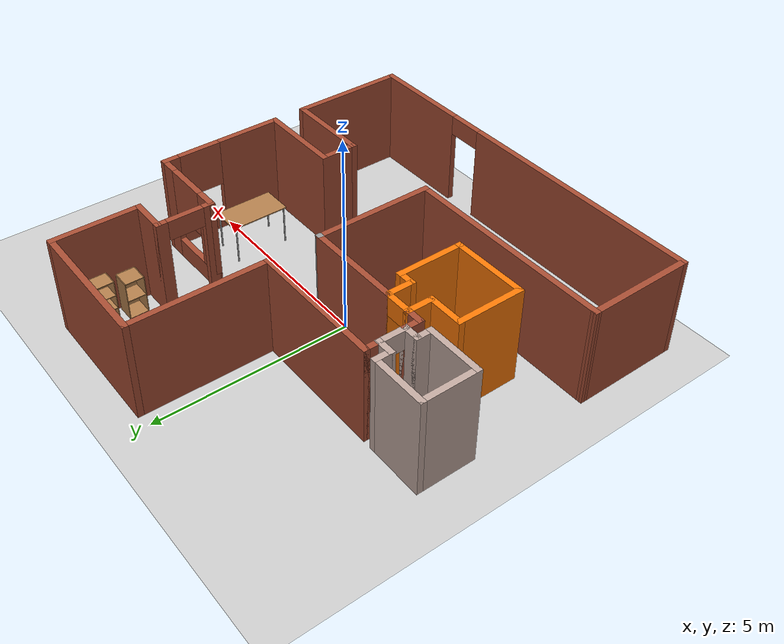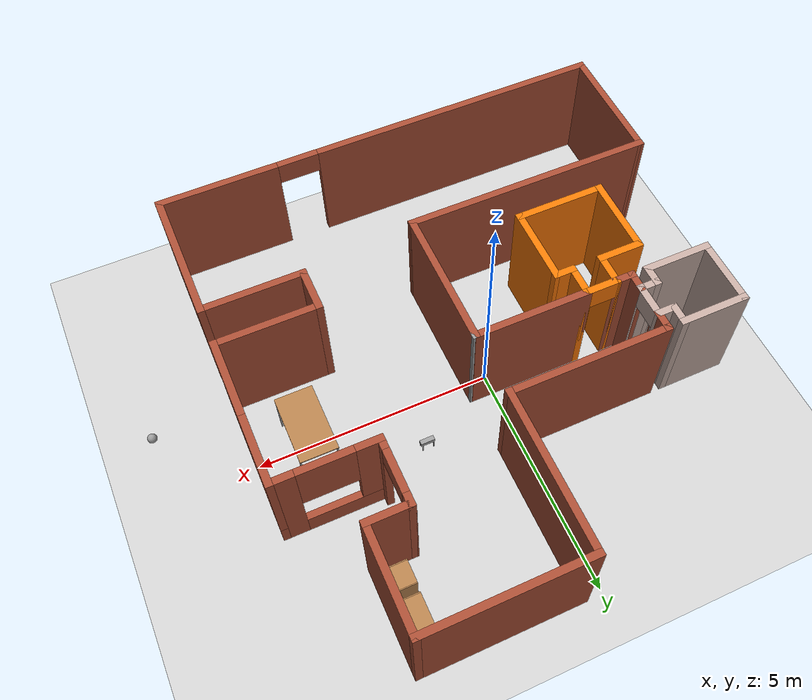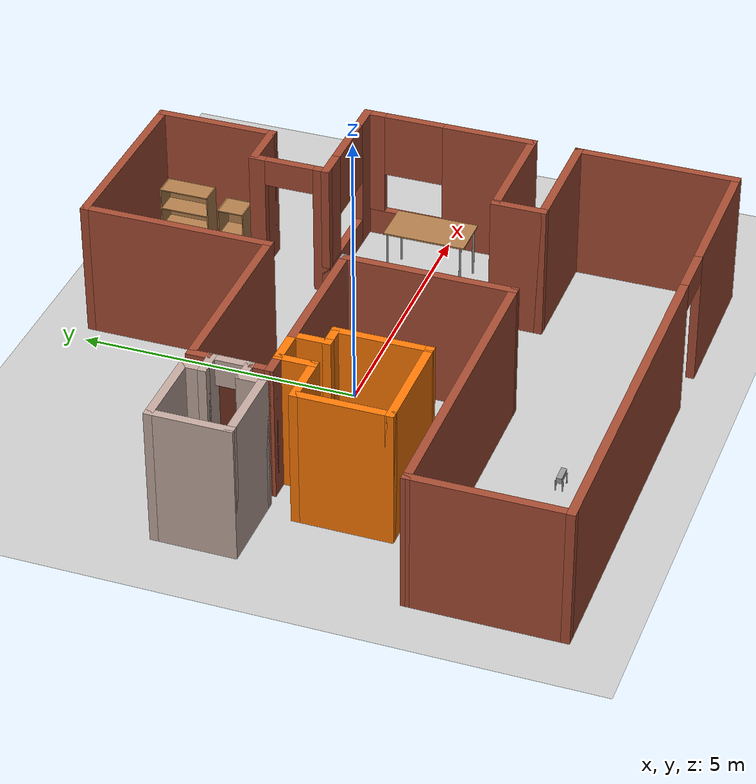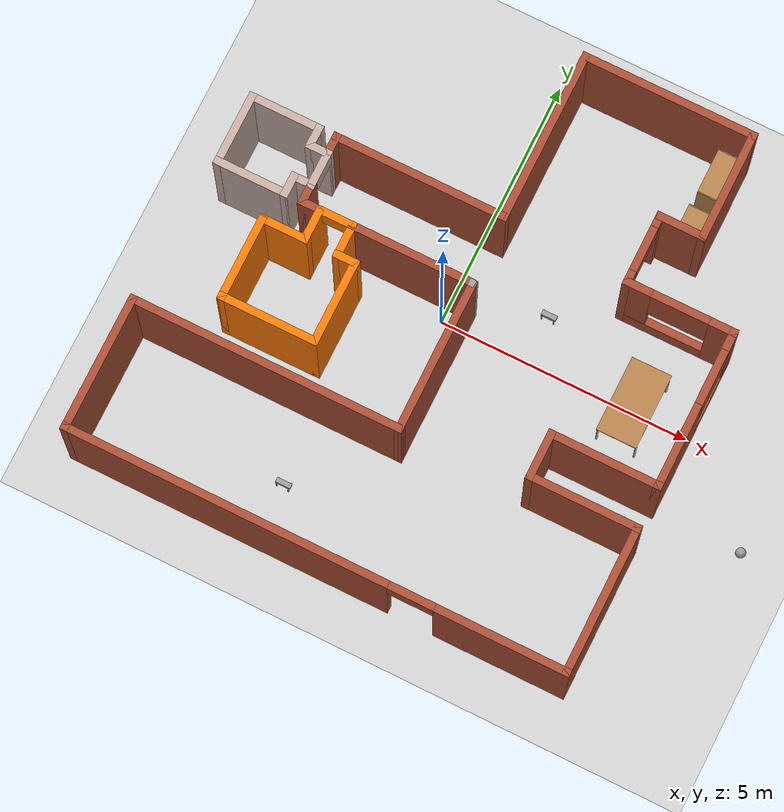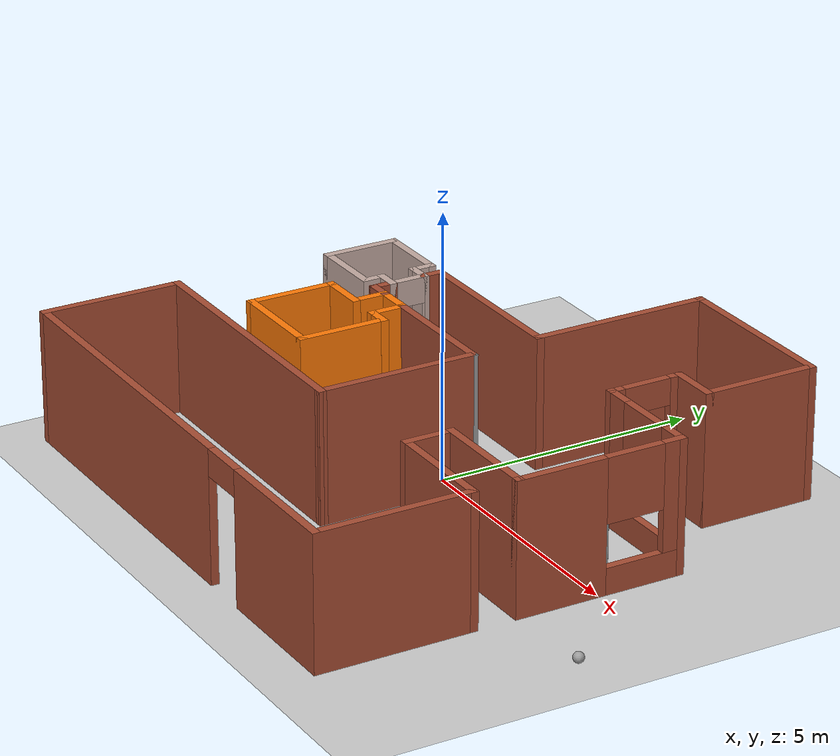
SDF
<sdf version="1.6">
 <world name="default">
  <plugin name="hello" filename="libhello.so"/>
  <light name="sun" type="directional">
   <pose>0 0 10 0 -0 0</pose>
   <diffuse>0.8 0.8 0.8 1</diffuse>
   <specular>0.2 0.2 0.2 1</specular>
   <attenuation>
    <range>1000</range>
    <constant>0.9</constant>
    <linear>0.01</linear>
    <quadratic>0.001</quadratic>
   </attenuation>
   <direction>-0.5 0.1 -0.9</direction>
  </light>
  <model name="ground_plane">
   <static>1</static>
   <link name="link">
    <collision name="collision">
     <geometry><plane><normal>0 0 1</normal><size>100 100</size></plane></geometry>
     <surface>
      <contact><collide_bitmask>65535</collide_bitmask></contact>
      <friction><ode><mu>100</mu><mu2>50</mu2></ode></friction>
     </surface>
    </collision>
    <visual name="visual">
     <cast_shadows>0</cast_shadows>
     <geometry><plane><normal>0 0 1</normal><size>100 100</size></plane></geometry>
     <material>
      <script><uri>file://media/materials/scripts/gazebo.material</uri><name>Gazebo/Grey</name></script>
     </material>
    </visual>
   </link>
  </model>
  <gravity>0 0 -9.8</gravity>
  <magnetic_field>6e-06 2.3e-05 -4.2e-05</magnetic_field>
  <atmosphere type="adiabatic"/>
  <physics name="default_physics" default="0" type="ode">
   <max_step_size>0.001</max_step_size>
   <real_time_factor>1</real_time_factor>
   <real_time_update_rate>1000</real_time_update_rate>
  </physics>
  <scene><ambient>0.4 0.4 0.4 1</ambient><background>0.7 0.7 0.7 1</background><shadows>1</shadows></scene>
  <spherical_coordinates>
   <surface_model>EARTH_WGS84</surface_model>
   <latitude_deg>0</latitude_deg>
   <longitude_deg>0</longitude_deg>
   <elevation>0</elevation>
   <heading_deg>0</heading_deg>
  </spherical_coordinates>
  <model name="home">
   <pose>0.07564 -0.09647 0 0 -0 0</pose>
   <link name="Wall_10">
    <collision name="Wall_10_Collision">
     <geometry><box><size>2.25 0.15 2.5</size></box></geometry>
     <pose>0 0 1.25 0 -0 0</pose>
    </collision>
    <visual name="Wall_10_Visual">
     <pose>0 0 1.25 0 -0 0</pose>
     <geometry><box><size>2.25 0.15 2.5</size></box></geometry>
     <material>
      <script><uri>file://media/materials/scripts/gazebo.material</uri><name>Gazebo/Bricks</name></script>
      <ambient>1 1 1 1</ambient>
     </material>
     <meta><layer>0</layer></meta>
    </visual>
    <pose>3.67503 4.075 0 0 -0 1.5708</pose>
   </link>
   <link name="Wall_11">
    <collision name="Wall_11_Collision">
     <geometry><box><size>3.5 0.15 2.5</size></box></geometry>
     <pose>0 0 1.25 0 -0 0</pose>
    </collision>
    <visual name="Wall_11_Visual">
     <pose>0 0 1.25 0 -0 0</pose>
     <geometry><box><size>3.5 0.15 2.5</size></box></geometry>
     <material>
      <script><uri>file://media/materials/scripts/gazebo.material</uri><name>Gazebo/Bricks</name></script>
      <ambient>1 1 1 1</ambient>
     </material>
     <meta><layer>0</layer></meta>
    </visual>
    <pose>2.00003 5.125 0 0 -0 3.14159</pose>
   </link>
   <link name="Wall_12">
    <collision name="Wall_12_Collision">
     <geometry><box><size>3.5 0.15 2.5</size></box></geometry>
     <pose>0 0 1.25 0 -0 0</pose>
    </collision>
    <visual name="Wall_12_Visual">
     <pose>0 0 1.25 0 -0 0</pose>
     <geometry><box><size>3.5 0.15 2.5</size></box></geometry>
     <material>
      <script><uri>file://media/materials/scripts/gazebo.material</uri><name>Gazebo/Bricks</name></script>
      <ambient>1 1 1 1</ambient>
     </material>
     <meta><layer>0</layer></meta>
    </visual>
    <pose>0.325032 3.45 0 0 0 -1.5708</pose>
   </link>
   <link name="Wall_13">
    <collision name="Wall_13_Collision">
     <geometry><box><size>3.5 0.15 2.5</size></box></geometry>
     <pose>0 0 1.25 0 -0 0</pose>
    </collision>
    <visual name="Wall_13_Visual">
     <pose>0 0 1.25 0 -0 0</pose>
     <geometry><box><size>3.5 0.15 2.5</size></box></geometry>
     <material>
      <script><uri>file://media/materials/scripts/gazebo.material</uri><name>Gazebo/Bricks</name></script>
      <ambient>1 1 1 1</ambient>
     </material>
     <meta><layer>0</layer></meta>
    </visual>
    <pose>-1.34997 1.775 0 0 -0 3.14159</pose>
   </link>
   <link name="Wall_14">
    <collision name="Wall_14_Collision">
     <geometry><box><size>0.5 0.15 2.5</size></box></geometry>
     <pose>0 0 1.25 0 -0 0</pose>
    </collision>
    <visual name="Wall_14_Visual">
     <pose>0 0 1.25 0 -0 0</pose>
     <geometry><box><size>0.5 0.15 2.5</size></box></geometry>
     <material>
      <script><uri>file://media/materials/scripts/gazebo.material</uri><name>Gazebo/Bricks</name></script>
      <ambient>1 1 1 1</ambient>
     </material>
     <meta><layer>0</layer></meta>
    </visual>
    <pose>-3.02497 1.6 0 0 0 -1.5708</pose>
   </link>
   <link name="Wall_15">
    <collision name="Wall_15_Collision">
     <geometry><box><size>0.5 0.15 2.5</size></box></geometry>
     <pose>0 0 1.25 0 -0 0</pose>
    </collision>
    <visual name="Wall_15_Visual">
     <pose>0 0 1.25 0 -0 0</pose>
     <geometry><box><size>0.5 0.15 2.5</size></box></geometry>
     <material>
      <script><uri>file://media/materials/scripts/gazebo.material</uri><name>Gazebo/Grey</name></script>
      <ambient>0.760784 0.662745 0.627451 1</ambient>
     </material>
     <meta><layer>0</layer></meta>
    </visual>
    <pose>-3.19997 1.425 0 0 -0 3.14159</pose>
   </link>
   <link name="Wall_16">
    <collision name="Wall_16_Collision">
     <geometry><box><size>0.5 0.15 2.5</size></box></geometry>
     <pose>0 0 1.25 0 -0 0</pose>
    </collision>
    <visual name="Wall_16_Visual">
     <pose>0 0 1.25 0 -0 0</pose>
     <geometry><box><size>0.5 0.15 2.5</size></box></geometry>
     <material>
      <script><uri>file://media/materials/scripts/gazebo.material</uri><name>Gazebo/Grey</name></script>
      <ambient>0.760784 0.662745 0.627451 1</ambient>
     </material>
     <meta><layer>0</layer></meta>
    </visual>
    <pose>-3.37497 1.6 0 0 -0 1.5708</pose>
   </link>
   <link name="Wall_17">
    <collision name="Wall_17_Collision">
     <geometry><box><size>1.5 0.15 2.5</size></box></geometry>
     <pose>0 0 1.25 0 -0 0</pose>
    </collision>
    <visual name="Wall_17_Visual">
     <pose>0 0 1.25 0 -0 0</pose>
     <geometry><box><size>1.5 0.15 2.5</size></box></geometry>
     <material>
      <script><uri>file://media/materials/scripts/gazebo.material</uri><name>Gazebo/Grey</name></script>
      <ambient>0.760784 0.662745 0.627451 1</ambient>
     </material>
     <meta><layer>0</layer></meta>
    </visual>
    <pose>-4.04997 1.775 0 0 -0 3.14159</pose>
   </link>
   <link name="Wall_18">
    <collision name="Wall_18_Collision">
     <geometry><box><size>1.5 0.15 2.5</size></box></geometry>
     <pose>0 0 1.25 0 -0 0</pose>
    </collision>
    <visual name="Wall_18_Visual">
     <pose>0 0 1.25 0 -0 0</pose>
     <geometry><box><size>1.5 0.15 2.5</size></box></geometry>
     <material>
      <script><uri>file://media/materials/scripts/gazebo.material</uri><name>Gazebo/Grey</name></script>
      <ambient>0.760784 0.662745 0.627451 1</ambient>
     </material>
     <meta><layer>0</layer></meta>
    </visual>
    <pose>-4.72497 1.1 0 0 0 -1.5708</pose>
   </link>
   <link name="Wall_19">
    <collision name="Wall_19_Collision">
     <geometry><box><size>1.5 0.15 2.5</size></box></geometry>
     <pose>0 0 1.25 0 -0 0</pose>
    </collision>
    <visual name="Wall_19_Visual">
     <pose>0 0 1.25 0 -0 0</pose>
     <geometry><box><size>1.5 0.15 2.5</size></box></geometry>
     <material>
      <script><uri>file://media/materials/scripts/gazebo.material</uri><name>Gazebo/Grey</name></script>
      <ambient>0.760784 0.662745 0.627451 1</ambient>
     </material>
     <meta><layer>0</layer></meta>
    </visual>
    <pose>-4.04997 0.425 0 0 -0 0</pose>
   </link>
   <link name="Wall_2">
    <collision name="Wall_2_Collision">
     <geometry><box><size>3 0.15 2.5</size></box></geometry>
     <pose>0 0 1.25 0 -0 0</pose>
    </collision>
    <visual name="Wall_2_Visual">
     <pose>0 0 1.25 0 -0 0</pose>
     <geometry><box><size>3 0.15 2.5</size></box></geometry>
     <material>
      <script><uri>file://media/materials/scripts/gazebo.material</uri><name>Gazebo/Bricks</name></script>
      <ambient>1 1 1 1</ambient>
     </material>
     <meta><layer>0</layer></meta>
    </visual>
    <pose>4.92503 -3.7 0 0 -0 1.5708</pose>
   </link>
   <link name="Wall_20">
    <collision name="Wall_20_Collision">
     <geometry><box><size>0.5 0.15 2.5</size></box></geometry>
     <pose>0 0 1.25 0 -0 0</pose>
    </collision>
    <visual name="Wall_20_Visual">
     <pose>0 0 1.25 0 -0 0</pose>
     <geometry><box><size>0.5 0.15 2.5</size></box></geometry>
     <material>
      <script><uri>file://media/materials/scripts/gazebo.material</uri><name>Gazebo/Grey</name></script>
      <ambient>0.760784 0.662745 0.627451 1</ambient>
     </material>
     <meta><layer>0</layer></meta>
    </visual>
    <pose>-3.37497 0.6 0 0 -0 1.5708</pose>
   </link>
   <link name="Wall_21">
    <collision name="Wall_21_Collision">
     <geometry><box><size>0.5 0.15 2.5</size></box></geometry>
     <pose>0 0 1.25 0 -0 0</pose>
    </collision>
    <visual name="Wall_21_Visual">
     <pose>0 0 1.25 0 -0 0</pose>
     <geometry><box><size>0.5 0.15 2.5</size></box></geometry>
     <material>
      <script><uri>file://media/materials/scripts/gazebo.material</uri><name>Gazebo/Grey</name></script>
      <ambient>0.760784 0.662745 0.627451 1</ambient>
     </material>
     <meta><layer>0</layer></meta>
    </visual>
    <pose>-3.19997 0.775 0 0 -0 0</pose>
   </link>
   <link name="Wall_22">
    <collision name="Wall_22_Collision">
     <geometry><box><size>0.5 0.15 2.5</size></box></geometry>
     <pose>0 0 1.25 0 -0 0</pose>
    </collision>
    <visual name="Wall_22_Visual">
     <pose>0 0 1.25 0 -0 0</pose>
     <geometry><box><size>0.5 0.15 2.5</size></box></geometry>
     <material>
      <script><uri>file://media/materials/scripts/gazebo.material</uri><name>Gazebo/Bricks</name></script>
      <ambient>1 1 1 1</ambient>
     </material>
     <meta><layer>0</layer></meta>
    </visual>
    <pose>-3.02497 0.6 0 0 0 -1.5708</pose>
   </link>
   <link name="Wall_23">
    <collision name="Wall_23_Collision">
     <geometry><box><size>0.5 0.15 2.5</size></box></geometry>
     <pose>0 0 1.25 0 -0 0</pose>
    </collision>
    <visual name="Wall_23_Visual">
     <pose>0 0 1.25 0 -0 0</pose>
     <geometry><box><size>0.5 0.15 2.5</size></box></geometry>
     <material>
      <script><uri>file://media/materials/scripts/gazebo.material</uri><name>Gazebo/Bricks</name></script>
      <ambient>1 1 1 1</ambient>
     </material>
     <meta><layer>0</layer></meta>
    </visual>
    <pose>-2.84997 0.425 0 0 -0 0</pose>
   </link>
   <link name="Wall_24">
    <collision name="Wall_24_Collision">
     <geometry><box><size>0.75 0.15 2.5</size></box></geometry>
     <pose>0 0 1.25 0 -0 0</pose>
    </collision>
    <visual name="Wall_24_Visual">
     <pose>0 0 1.25 0 -0 0</pose>
     <geometry><box><size>0.75 0.15 2.5</size></box></geometry>
     <material>
      <script><uri>file://media/materials/scripts/gazebo.material</uri><name>Gazebo/Grey</name></script>
      <ambient>0.996078 0.47451 0.0196078 1</ambient>
     </material>
     <meta><layer>0</layer></meta>
    </visual>
    <pose>-2.67497 0.125 0 0 0 -1.5708</pose>
   </link>
   <link name="Wall_28">
    <collision name="Wall_28_Collision">
     <geometry><box><size>1 0.15 2.5</size></box></geometry>
     <pose>0 0 1.25 0 -0 0</pose>
    </collision>
    <visual name="Wall_28_Visual">
     <pose>0 0 1.25 0 -0 0</pose>
     <geometry><box><size>1 0.15 2.5</size></box></geometry>
     <material>
      <script><uri>file://media/materials/scripts/gazebo.material</uri><name>Gazebo/Grey</name></script>
      <ambient>0.996078 0.47451 0.0196078 1</ambient>
     </material>
     <meta><layer>0</layer></meta>
    </visual>
    <pose>-3.09997 -0.175 0 0 -0 3.14159</pose>
   </link>
   <link name="Wall_29">
    <collision name="Wall_29_Collision">
     <geometry><box><size>1.75 0.15 2.5</size></box></geometry>
     <pose>0 0 1.25 0 -0 0</pose>
    </collision>
    <visual name="Wall_29_Visual">
     <pose>0 0 1.25 0 -0 0</pose>
     <geometry><box><size>1.75 0.15 2.5</size></box></geometry>
     <material>
      <script><uri>file://media/materials/scripts/gazebo.material</uri><name>Gazebo/Grey</name></script>
      <ambient>0.996078 0.47451 0.0196078 1</ambient>
     </material>
     <meta><layer>0</layer></meta>
    </visual>
    <pose>-3.52497 -0.975 0 0 0 -1.5708</pose>
   </link>
   <link name="Wall_3">
    <collision name="Wall_3_Collision">
     <geometry><box><size>2.25 0.15 2.5</size></box></geometry>
     <pose>0 0 1.25 0 -0 0</pose>
    </collision>
    <visual name="Wall_3_Visual">
     <pose>0 0 1.25 0 -0 0</pose>
     <geometry><box><size>2.25 0.15 2.5</size></box></geometry>
     <material>
      <script><uri>file://media/materials/scripts/gazebo.material</uri><name>Gazebo/Bricks</name></script>
      <ambient>1 1 1 1</ambient>
     </material>
     <meta><layer>0</layer></meta>
    </visual>
    <pose>3.87503 -2.275 0 0 -0 3.14159</pose>
   </link>
   <link name="Wall_33">
    <collision name="Wall_33_Collision">
     <geometry><box><size>2 0.15 2.5</size></box></geometry>
     <pose>0 0 1.25 0 -0 0</pose>
    </collision>
    <visual name="Wall_33_Visual">
     <pose>0 0 1.25 0 -0 0</pose>
     <geometry><box><size>2 0.15 2.5</size></box></geometry>
     <material>
      <script><uri>file://media/materials/scripts/gazebo.material</uri><name>Gazebo/Grey</name></script>
      <ambient>0.996078 0.47451 0.0196078 1</ambient>
     </material>
     <meta><layer>0</layer></meta>
    </visual>
    <pose>-2.59997 -1.775 0 0 -0 0</pose>
   </link>
   <link name="Wall_34">
    <collision name="Wall_34_Collision">
     <geometry><box><size>1.75 0.15 2.5</size></box></geometry>
     <pose>0 0 1.25 0 -0 0</pose>
    </collision>
    <visual name="Wall_34_Visual">
     <pose>0 0 1.25 0 -0 0</pose>
     <geometry><box><size>1.75 0.15 2.5</size></box></geometry>
     <material>
      <script><uri>file://media/materials/scripts/gazebo.material</uri><name>Gazebo/Grey</name></script>
      <ambient>0.996078 0.47451 0.0196078 1</ambient>
     </material>
     <meta><layer>0</layer></meta>
    </visual>
    <pose>-1.67497 -0.975 0 0 -0 1.5708</pose>
   </link>
   <link name="Wall_35">
    <collision name="Wall_35_Collision">
     <geometry><box><size>0.5 0.15 2.5</size></box></geometry>
     <pose>0 0 1.25 0 -0 0</pose>
    </collision>
    <visual name="Wall_35_Visual">
     <pose>0 0 1.25 0 -0 0</pose>
     <geometry><box><size>0.5 0.15 2.5</size></box></geometry>
     <material>
      <script><uri>file://media/materials/scripts/gazebo.material</uri><name>Gazebo/Grey</name></script>
      <ambient>0.996078 0.47451 0.0196078 1</ambient>
     </material>
     <meta><layer>0</layer></meta>
    </visual>
    <pose>-1.84997 -0.175 0 0 -0 3.14159</pose>
   </link>
   <link name="Wall_36">
    <collision name="Wall_36_Collision">
     <geometry><box><size>0.75 0.15 2.5</size></box></geometry>
     <pose>0 0 1.25 0 -0 0</pose>
    </collision>
    <visual name="Wall_36_Visual">
     <pose>0 0 1.25 0 -0 0</pose>
     <geometry><box><size>0.75 0.15 2.5</size></box></geometry>
     <material>
      <script><uri>file://media/materials/scripts/gazebo.material</uri><name>Gazebo/Grey</name></script>
      <ambient>0.996078 0.47451 0.0196078 1</ambient>
     </material>
     <meta><layer>0</layer></meta>
    </visual>
    <pose>-2.02497 0.125 0 0 -0 1.5708</pose>
   </link>
   <link name="Wall_37">
    <collision name="Wall_37_Collision">
     <geometry><box><size>2.5 0.15 2.5</size></box></geometry>
     <pose>0 0 1.25 0 -0 0</pose>
    </collision>
    <visual name="Wall_37_Visual">
     <pose>0 0 1.25 0 -0 0</pose>
     <geometry><box><size>2.5 0.15 2.5</size></box></geometry>
     <material>
      <script><uri>file://media/materials/scripts/gazebo.material</uri><name>Gazebo/Bricks</name></script>
      <ambient>1 1 1 1</ambient>
     </material>
     <meta><layer>0</layer></meta>
    </visual>
    <pose>-0.849968 0.425 0 0 -0 0</pose>
   </link>
   <link name="Wall_4">
    <collision name="Wall_4_Collision">
     <geometry><box><size>1 0.15 2.5</size></box></geometry>
     <pose>0 0 1.25 0 -0 0</pose>
    </collision>
    <visual name="Wall_4_Visual">
     <pose>0 0 1.25 0 -0 0</pose>
     <geometry><box><size>1 0.15 2.5</size></box></geometry>
     <material>
      <script><uri>file://media/materials/scripts/gazebo.material</uri><name>Gazebo/Bricks</name></script>
      <ambient>1 1 1 1</ambient>
     </material>
     <meta><layer>0</layer></meta>
    </visual>
    <pose>2.82503 -1.85 0 0 -0 1.5708</pose>
   </link>
   <link name="Wall_43">
    <pose>3.2e-05 -5.125 0 0 -0 3.14159</pose>
    <visual name="Wall_43_Visual_0">
     <pose>-3.68092 0 1.25 0 -0 0</pose>
     <geometry><box><size>2.63816 0.15 2.5</size></box></geometry>
     <material>
      <script><uri>file://media/materials/scripts/gazebo.material</uri><name>Gazebo/Bricks</name></script>
      <ambient>1 1 1 1</ambient>
     </material>
     <meta><layer>0</layer></meta>
    </visual>
    <collision name="Wall_43_Collision_0">
     <geometry><box><size>2.63816 0.15 2.5</size></box></geometry>
     <pose>-3.68092 0 1.25 0 -0 0</pose>
    </collision>
    <visual name="Wall_43_Visual_1">
     <pose>1.76908 0 1.25 0 -0 0</pose>
     <geometry><box><size>6.46184 0.15 2.5</size></box></geometry>
     <material>
      <script><uri>file://media/materials/scripts/gazebo.material</uri><name>Gazebo/Bricks</name></script>
      <ambient>1 1 1 1</ambient>
     </material>
     <meta><layer>0</layer></meta>
    </visual>
    <collision name="Wall_43_Collision_1">
     <geometry><box><size>6.46184 0.15 2.5</size></box></geometry>
     <pose>1.76908 0 1.25 0 -0 0</pose>
    </collision>
    <visual name="Wall_43_Visual_2">
     <pose>-1.91184 0 2.25 0 -0 0</pose>
     <geometry><box><size>0.9 0.15 0.5</size></box></geometry>
     <material>
      <script><uri>file://media/materials/scripts/gazebo.material</uri><name>Gazebo/Bricks</name></script>
      <ambient>1 1 1 1</ambient>
     </material>
     <meta><layer>0</layer></meta>
    </visual>
    <collision name="Wall_43_Collision_2">
     <geometry><box><size>0.9 0.15 0.5</size></box></geometry>
     <pose>-1.91184 0 2.25 0 -0 0</pose>
    </collision>
   </link>
   <link name="Wall_44">
    <collision name="Wall_44_Collision">
     <geometry><box><size>2.75 0.15 2.5</size></box></geometry>
     <pose>0 0 1.25 0 -0 0</pose>
    </collision>
    <visual name="Wall_44_Visual">
     <pose>0 0 1.25 0 -0 0</pose>
     <geometry><box><size>2.75 0.15 2.5</size></box></geometry>
     <material>
      <script><uri>file://media/materials/scripts/gazebo.material</uri><name>Gazebo/Bricks</name></script>
      <ambient>1 1 1 1</ambient>
     </material>
     <meta><layer>0</layer></meta>
    </visual>
    <pose>-4.92497 -3.825 0 0 -0 1.5708</pose>
   </link>
   <link name="Wall_48">
    <collision name="Wall_48_Collision">
     <geometry><box><size>5.45338 0.15 2.5</size></box></geometry>
     <pose>0 0 1.25 0 -0 0</pose>
    </collision>
    <visual name="Wall_48_Visual">
     <pose>0 0 1.25 0 -0 0</pose>
     <geometry><box><size>5.45338 0.15 2.5</size></box></geometry>
     <material>
      <script><uri>file://media/materials/scripts/gazebo.material</uri><name>Gazebo/Bricks</name></script>
      <ambient>1 1 1 1</ambient>
     </material>
     <meta><layer>0</layer></meta>
    </visual>
    <pose>-2.27328 -2.52727 0 0 0 -0.000856</pose>
   </link>
   <link name="Wall_49">
    <collision name="Wall_49_Collision">
     <geometry><box><size>3.09697 0.15 2.5</size></box></geometry>
     <pose>0 0 1.25 0 -0 0</pose>
    </collision>
    <visual name="Wall_49_Visual">
     <pose>0 0 1.25 0 -0 0</pose>
     <geometry><box><size>3.09697 0.15 2.5</size></box></geometry>
     <material>
      <script><uri>file://media/materials/scripts/gazebo.material</uri><name>Gazebo/Bricks</name></script>
      <ambient>1 1 1 1</ambient>
     </material>
     <meta><layer>0</layer></meta>
    </visual>
    <pose>0.375849 -1.05607 0 0 -0 1.57254</pose>
   </link>
   <link name="Wall_5">
    <collision name="Wall_5_Collision">
     <geometry><box><size>2.25 0.15 2.5</size></box></geometry>
     <pose>0 0 1.25 0 -0 0</pose>
    </collision>
    <visual name="Wall_5_Visual">
     <pose>0 0 1.25 0 -0 0</pose>
     <geometry><box><size>2.25 0.15 2.5</size></box></geometry>
     <material>
      <script><uri>file://media/materials/scripts/gazebo.material</uri><name>Gazebo/Bricks</name></script>
      <ambient>1 1 1 1</ambient>
     </material>
     <meta><layer>0</layer></meta>
    </visual>
    <pose>3.87503 -1.425 0 0 -0 0</pose>
   </link>
   <link name="Wall_52">
    <collision name="Wall_52_Collision">
     <geometry><box><size>0.15 0.15 2.5</size></box></geometry>
     <pose>0 0 1.25 0 -0 0</pose>
    </collision>
    <visual name="Wall_52_Visual">
     <pose>0 0 1.25 0 -0 0</pose>
     <geometry><box><size>0.15 0.15 2.5</size></box></geometry>
     <material>
      <script><uri>file://media/materials/scripts/gazebo.material</uri><name>Gazebo/Grey</name></script>
      <ambient>1 1 1 1</ambient>
     </material>
     <meta><layer>0</layer></meta>
    </visual>
    <pose>0.373287 0.421097 0 0 -0 0</pose>
   </link>
   <link name="Wall_55">
    <pose>-3.02497 1.1 0 0 0 -1.5708</pose>
    <visual name="Wall_55_Visual_0">
     <pose>-0.354187 0 1.25 0 -0 0</pose>
     <geometry><box><size>0.091626 0.15 2.5</size></box></geometry>
     <material>
      <script><uri>file://media/materials/scripts/gazebo.material</uri><name>Gazebo/Grey</name></script>
      <ambient>0.760784 0.662745 0.627451 1</ambient>
     </material>
     <meta><layer>0</layer></meta>
    </visual>
    <collision name="Wall_55_Collision_0">
     <geometry><box><size>0.091626 0.15 2.5</size></box></geometry>
     <pose>-0.354187 0 1.25 0 -0 0</pose>
    </collision>
    <visual name="Wall_55_Visual_1">
     <pose>0.362229 0 1.25 0 -0 0</pose>
     <geometry><box><size>0.075541 0.15 2.5</size></box></geometry>
     <material>
      <script><uri>file://media/materials/scripts/gazebo.material</uri><name>Gazebo/Grey</name></script>
      <ambient>0.760784 0.662745 0.627451 1</ambient>
     </material>
     <meta><layer>0</layer></meta>
    </visual>
    <collision name="Wall_55_Collision_1">
     <geometry><box><size>0.075541 0.15 2.5</size></box></geometry>
     <pose>0.362229 0 1.25 0 -0 0</pose>
    </collision>
    <visual name="Wall_55_Visual_2">
     <pose>0.008042 0 2.25 0 -0 0</pose>
     <geometry><box><size>0.632833 0.15 0.5</size></box></geometry>
     <material>
      <script><uri>file://media/materials/scripts/gazebo.material</uri><name>Gazebo/Grey</name></script>
      <ambient>0.760784 0.662745 0.627451 1</ambient>
     </material>
     <meta><layer>0</layer></meta>
    </visual>
    <collision name="Wall_55_Collision_2">
     <geometry><box><size>0.632833 0.15 0.5</size></box></geometry>
     <pose>0.008042 0 2.25 0 -0 0</pose>
    </collision>
   </link>
   <link name="Wall_57">
    <pose>-2.34997 0.425 0 0 -0 0</pose>
    <visual name="Wall_57_Visual_0">
     <pose>-0.365442 0 1.25 0 -0 0</pose>
     <geometry><box><size>0.069115 0.15 2.5</size></box></geometry>
     <material>
      <script><uri>file://media/materials/scripts/gazebo.material</uri><name>Gazebo/Grey</name></script>
      <ambient>0.996078 0.47451 0.0196078 1</ambient>
     </material>
     <meta><layer>0</layer></meta>
    </visual>
    <collision name="Wall_57_Collision_0">
     <geometry><box><size>0.069115 0.15 2.5</size></box></geometry>
     <pose>-0.365442 0 1.25 0 -0 0</pose>
    </collision>
    <visual name="Wall_57_Visual_1">
     <pose>0.355623 0 1.25 0 -0 0</pose>
     <geometry><box><size>0.088753 0.15 2.5</size></box></geometry>
     <material>
      <script><uri>file://media/materials/scripts/gazebo.material</uri><name>Gazebo/Grey</name></script>
      <ambient>0.996078 0.47451 0.0196078 1</ambient>
     </material>
     <meta><layer>0</layer></meta>
    </visual>
    <collision name="Wall_57_Collision_1">
     <geometry><box><size>0.088753 0.15 2.5</size></box></geometry>
     <pose>0.355623 0 1.25 0 -0 0</pose>
    </collision>
    <visual name="Wall_57_Visual_2">
     <pose>-0.009819 0 2.25 0 -0 0</pose>
     <geometry><box><size>0.642131 0.15 0.5</size></box></geometry>
     <material>
      <script><uri>file://media/materials/scripts/gazebo.material</uri><name>Gazebo/Grey</name></script>
      <ambient>0.996078 0.47451 0.0196078 1</ambient>
     </material>
     <meta><layer>0</layer></meta>
    </visual>
    <collision name="Wall_57_Collision_2">
     <geometry><box><size>0.642131 0.15 0.5</size></box></geometry>
     <pose>-0.009819 0 2.25 0 -0 0</pose>
    </collision>
   </link>
   <link name="Wall_6">
    <pose>4.92503 0.125 0 0 -0 1.5708</pose>
    <visual name="Wall_6_Visual_0">
     <pose>-0.764074 0 1.25 0 -0 0</pose>
     <geometry><box><size>1.72185 0.15 2.5</size></box></geometry>
     <material>
      <script><uri>file://media/materials/scripts/gazebo.material</uri><name>Gazebo/Bricks</name></script>
      <ambient>1 1 1 1</ambient>
     </material>
     <meta><layer>0</layer></meta>
    </visual>
    <collision name="Wall_6_Collision_0">
     <geometry><box><size>1.72185 0.15 2.5</size></box></geometry>
     <pose>-0.764074 0 1.25 0 -0 0</pose>
    </collision>
    <visual name="Wall_6_Visual_1">
     <pose>0.860926 0 0.25 0 -0 0</pose>
     <geometry><box><size>1.52815 0.15 0.5</size></box></geometry>
     <material>
      <script><uri>file://media/materials/scripts/gazebo.material</uri><name>Gazebo/Bricks</name></script>
      <ambient>1 1 1 1</ambient>
     </material>
     <meta><layer>0</layer></meta>
    </visual>
    <collision name="Wall_6_Collision_1">
     <geometry><box><size>1.52815 0.15 0.5</size></box></geometry>
     <pose>0.860926 0 0.25 0 -0 0</pose>
    </collision>
    <visual name="Wall_6_Visual_2">
     <pose>1.40882 0 1.5 0 -0 0</pose>
     <geometry><box><size>0.432369 0.15 2</size></box></geometry>
     <material>
      <script><uri>file://media/materials/scripts/gazebo.material</uri><name>Gazebo/Bricks</name></script>
      <ambient>1 1 1 1</ambient>
     </material>
     <meta><layer>0</layer></meta>
    </visual>
    <collision name="Wall_6_Collision_2">
     <geometry><box><size>0.432369 0.15 2</size></box></geometry>
     <pose>1.40882 0 1.5 0 -0 0</pose>
    </collision>
    <visual name="Wall_6_Visual_3">
     <pose>0.644742 0 1.9 0 -0 0</pose>
     <geometry><box><size>1.09578 0.15 1.2</size></box></geometry>
     <material>
      <script><uri>file://media/materials/scripts/gazebo.material</uri><name>Gazebo/Bricks</name></script>
      <ambient>1 1 1 1</ambient>
     </material>
     <meta><layer>0</layer></meta>
    </visual>
    <collision name="Wall_6_Collision_3">
     <geometry><box><size>1.09578 0.15 1.2</size></box></geometry>
     <pose>0.644742 0 1.9 0 -0 0</pose>
    </collision>
   </link>
   <link name="Wall_7">
    <pose>3.87503 1.675 0 0 -0 3.14159</pose>
    <visual name="Wall_7_Visual_0">
     <pose>-0.852878 0 1.25 0 -0 0</pose>
     <geometry><box><size>0.544245 0.15 2.5</size></box></geometry>
     <material>
      <script><uri>file://media/materials/scripts/gazebo.material</uri><name>Gazebo/Bricks</name></script>
      <ambient>1 1 1 1</ambient>
     </material>
     <meta><layer>0</layer></meta>
    </visual>
    <collision name="Wall_7_Collision_0">
     <geometry><box><size>0.544245 0.15 2.5</size></box></geometry>
     <pose>-0.852878 0 1.25 0 -0 0</pose>
    </collision>
    <visual name="Wall_7_Visual_1">
     <pose>0.272122 0 0.25 0 -0 0</pose>
     <geometry><box><size>1.70575 0.15 0.5</size></box></geometry>
     <material>
      <script><uri>file://media/materials/scripts/gazebo.material</uri><name>Gazebo/Bricks</name></script>
      <ambient>1 1 1 1</ambient>
     </material>
     <meta><layer>0</layer></meta>
    </visual>
    <collision name="Wall_7_Collision_1">
     <geometry><box><size>1.70575 0.15 0.5</size></box></geometry>
     <pose>0.272122 0 0.25 0 -0 0</pose>
    </collision>
    <visual name="Wall_7_Visual_2">
     <pose>0.841009 0 1.5 0 -0 0</pose>
     <geometry><box><size>0.567982 0.15 2</size></box></geometry>
     <material>
      <script><uri>file://media/materials/scripts/gazebo.material</uri><name>Gazebo/Bricks</name></script>
      <ambient>1 1 1 1</ambient>
     </material>
     <meta><layer>0</layer></meta>
    </visual>
    <collision name="Wall_7_Collision_2">
     <geometry><box><size>0.567982 0.15 2</size></box></geometry>
     <pose>0.841009 0 1.5 0 -0 0</pose>
    </collision>
    <visual name="Wall_7_Visual_3">
     <pose>-0.011869 0 1.9 0 -0 0</pose>
     <geometry><box><size>1.13777 0.15 1.2</size></box></geometry>
     <material>
      <script><uri>file://media/materials/scripts/gazebo.material</uri><name>Gazebo/Bricks</name></script>
      <ambient>1 1 1 1</ambient>
     </material>
     <meta><layer>0</layer></meta>
    </visual>
    <collision name="Wall_7_Collision_3">
     <geometry><box><size>1.13777 0.15 1.2</size></box></geometry>
     <pose>-0.011869 0 1.9 0 -0 0</pose>
    </collision>
   </link>
   <link name="Wall_8">
    <pose>2.82503 2.35 0 0 -0 1.5708</pose>
    <visual name="Wall_8_Visual_0">
     <pose>-0.598383 0 1.25 0 -0 0</pose>
     <geometry><box><size>0.303235 0.15 2.5</size></box></geometry>
     <material>
      <script><uri>file://media/materials/scripts/gazebo.material</uri><name>Gazebo/Bricks</name></script>
      <ambient>1 1 1 1</ambient>
     </material>
     <meta><layer>0</layer></meta>
    </visual>
    <collision name="Wall_8_Collision_0">
     <geometry><box><size>0.303235 0.15 2.5</size></box></geometry>
     <pose>-0.598383 0 1.25 0 -0 0</pose>
    </collision>
    <visual name="Wall_8_Visual_1">
     <pose>0.601617 0 1.25 0 -0 0</pose>
     <geometry><box><size>0.296765 0.15 2.5</size></box></geometry>
     <material>
      <script><uri>file://media/materials/scripts/gazebo.material</uri><name>Gazebo/Bricks</name></script>
      <ambient>1 1 1 1</ambient>
     </material>
     <meta><layer>0</layer></meta>
    </visual>
    <collision name="Wall_8_Collision_1">
     <geometry><box><size>0.296765 0.15 2.5</size></box></geometry>
     <pose>0.601617 0 1.25 0 -0 0</pose>
    </collision>
    <visual name="Wall_8_Visual_2">
     <pose>0.003235 0 2.25 0 -0 0</pose>
     <geometry><box><size>0.9 0.15 0.5</size></box></geometry>
     <material>
      <script><uri>file://media/materials/scripts/gazebo.material</uri><name>Gazebo/Bricks</name></script>
      <ambient>1 1 1 1</ambient>
     </material>
     <meta><layer>0</layer></meta>
    </visual>
    <collision name="Wall_8_Collision_2">
     <geometry><box><size>0.9 0.15 0.5</size></box></geometry>
     <pose>0.003235 0 2.25 0 -0 0</pose>
    </collision>
   </link>
   <link name="Wall_9">
    <collision name="Wall_9_Collision">
     <geometry><box><size>1 0.15 2.5</size></box></geometry>
     <pose>0 0 1.25 0 -0 0</pose>
    </collision>
    <visual name="Wall_9_Visual">
     <pose>0 0 1.25 0 -0 0</pose>
     <geometry><box><size>1 0.15 2.5</size></box></geometry>
     <material>
      <script><uri>file://media/materials/scripts/gazebo.material</uri><name>Gazebo/Bricks</name></script>
      <ambient>1 1 1 1</ambient>
     </material>
     <meta><layer>0</layer></meta>
    </visual>
    <pose>3.25003 3.025 0 0 -0 0</pose>
   </link>
   <static>1</static>
  </model>
  <model name="table">
   <static>1</static>
   <link name="link">
    <collision name="surface">
     <pose>0 0 1 0 -0 0</pose>
     <geometry><box><size>1.5 0.8 0.03</size></box></geometry>
     <surface><friction><ode><mu>0.6</mu><mu2>0.6</mu2></ode></friction></surface>
    </collision>
    <visual name="visual1">
     <pose>0 0 1 0 -0 0</pose>
     <geometry><box><size>1.5 0.8 0.03</size></box></geometry>
     <material>
      <script><uri>file://media/materials/scripts/gazebo.material</uri><name>Gazebo/Wood</name></script>
     </material>
    </visual>
    <collision name="front_left_leg">
     <pose>0.68 0.38 0.5 0 -0 0</pose>
     <geometry><cylinder><radius>0.02</radius><length>1</length></cylinder></geometry>
    </collision>
    <visual name="front_left_leg">
     <pose>0.68 0.38 0.5 0 -0 0</pose>
     <geometry><cylinder><radius>0.02</radius><length>1</length></cylinder></geometry>
     <material>
      <script><uri>file://media/materials/scripts/gazebo.material</uri><name>Gazebo/Grey</name></script>
     </material>
    </visual>
    <collision name="front_right_leg">
     <pose>0.68 -0.38 0.5 0 -0 0</pose>
     <geometry><cylinder><radius>0.02</radius><length>1</length></cylinder></geometry>
    </collision>
    <visual name="front_right_leg">
     <pose>0.68 -0.38 0.5 0 -0 0</pose>
     <geometry><cylinder><radius>0.02</radius><length>1</length></cylinder></geometry>
     <material>
      <script><uri>file://media/materials/scripts/gazebo.material</uri><name>Gazebo/Grey</name></script>
     </material>
    </visual>
    <collision name="back_right_leg">
     <pose>-0.68 -0.38 0.5 0 -0 0</pose>
     <geometry><cylinder><radius>0.02</radius><length>1</length></cylinder></geometry>
    </collision>
    <visual name="back_right_leg">
     <pose>-0.68 -0.38 0.5 0 -0 0</pose>
     <geometry><cylinder><radius>0.02</radius><length>1</length></cylinder></geometry>
     <material>
      <script><uri>file://media/materials/scripts/gazebo.material</uri><name>Gazebo/Grey</name></script>
     </material>
    </visual>
    <collision name="back_left_leg">
     <pose>-0.68 0.38 0.5 0 -0 0</pose>
     <geometry><cylinder><radius>0.02</radius><length>1</length></cylinder></geometry>
    </collision>
    <visual name="back_left_leg">
     <pose>-0.68 0.38 0.5 0 -0 0</pose>
     <geometry><cylinder><radius>0.02</radius><length>1</length></cylinder></geometry>
     <material>
      <script><uri>file://media/materials/scripts/gazebo.material</uri><name>Gazebo/Grey</name></script>
     </material>
    </visual>
   </link>
   <pose>3.88916 -0.019999 0 0 0 -1.5708</pose>
  </model>
  <model name="bookshelf">
   <static>1</static>
   <link name="link">
    <inertial><mass>1</mass></inertial>
    <collision name="back">
     <pose>0 0.005 0.6 0 -0 0</pose>
     <geometry><box><size>0.9 0.01 1.2</size></box></geometry>
    </collision>
    <visual name="visual1">
     <pose>0 0.005 0.6 0 -0 0</pose>
     <geometry><box><size>0.9 0.01 1.2</size></box></geometry>
     <material>
      <script><uri>file://media/materials/scripts/gazebo.material</uri><name>Gazebo/Wood</name></script>
     </material>
    </visual>
    <collision name="left_side">
     <pose>0.45 -0.195 0.6 0 -0 0</pose>
     <geometry><box><size>0.02 0.4 1.2</size></box></geometry>
    </collision>
    <visual name="visual2">
     <pose>0.45 -0.195 0.6 0 -0 0</pose>
     <geometry><box><size>0.02 0.4 1.2</size></box></geometry>
     <material>
      <script><uri>file://media/materials/scripts/gazebo.material</uri><name>Gazebo/Wood</name></script>
     </material>
    </visual>
    <collision name="right_side">
     <pose>-0.45 -0.195 0.6 0 -0 0</pose>
     <geometry><box><size>0.02 0.4 1.2</size></box></geometry>
    </collision>
    <visual name="visual3">
     <pose>-0.45 -0.195 0.6 0 -0 0</pose>
     <geometry><box><size>0.02 0.4 1.2</size></box></geometry>
     <material>
      <script><uri>file://media/materials/scripts/gazebo.material</uri><name>Gazebo/Wood</name></script>
     </material>
    </visual>
    <collision name="bottom">
     <pose>0 -0.195 0.03 0 -0 0</pose>
     <geometry><box><size>0.88 0.4 0.06</size></box></geometry>
    </collision>
    <visual name="visual4">
     <pose>0 -0.195 0.03 0 -0 0</pose>
     <geometry><box><size>0.88 0.4 0.06</size></box></geometry>
     <material>
      <script><uri>file://media/materials/scripts/gazebo.material</uri><name>Gazebo/Wood</name></script>
     </material>
    </visual>
    <collision name="top">
     <pose>0 -0.195 1.19 0 -0 0</pose>
     <geometry><box><size>0.88 0.4 0.02</size></box></geometry>
    </collision>
    <visual name="visual5">
     <pose>0 -0.195 1.19 0 -0 0</pose>
     <geometry><box><size>0.88 0.4 0.02</size></box></geometry>
     <material>
      <script><uri>file://media/materials/scripts/gazebo.material</uri><name>Gazebo/Wood</name></script>
     </material>
    </visual>
    <collision name="low_shelf">
     <pose>0 -0.195 0.43 0 -0 0</pose>
     <geometry><box><size>0.88 0.4 0.02</size></box></geometry>
    </collision>
    <visual name="visual6">
     <pose>0 -0.195 0.43 0 -0 0</pose>
     <geometry><box><size>0.88 0.4 0.02</size></box></geometry>
     <material>
      <script><uri>file://media/materials/scripts/gazebo.material</uri><name>Gazebo/Wood</name></script>
     </material>
    </visual>
    <collision name="high_shelf">
     <pose>0 -0.195 0.8 0 -0 0</pose>
     <geometry><box><size>0.88 0.4 0.02</size></box></geometry>
    </collision>
    <visual name="visual7">
     <pose>0 -0.195 0.8 0 -0 0</pose>
     <geometry><box><size>0.88 0.4 0.02</size></box></geometry>
     <material>
      <script><uri>file://media/materials/scripts/gazebo.material</uri><name>Gazebo/Wood</name></script>
     </material>
    </visual>
   </link>
   <pose>3.61995 4.45989 0 0 0 -1.5708</pose>
  </model>
  <model name="cabinet">
   <static>1</static>
   <link name="cabinet_bottom_plate">
    <inertial>
     <pose>0 0 -1 0 -0 0</pose>
     <inertia><ixx>2.05</ixx><ixy>0</ixy><ixz>0</ixz><iyy>2.05</iyy><iyz>0</iyz><izz>2.05</izz></inertia>
     <mass>25</mass>
    </inertial>
    <collision name="cabinet_bottom_plate_geom">
     <pose>0 0 0.01 0 -0 0</pose>
     <geometry><box><size>0.45 0.45 0.02</size></box></geometry>
    </collision>
    <visual name="cabinet_bottom_plate_geom_visual">
     <pose>0 0 0.01 0 -0 0</pose>
     <geometry><box><size>0.45 0.45 0.02</size></box></geometry>
     <material>
      <script><uri>file://media/materials/scripts/gazebo.material</uri><name>Gazebo/Wood</name></script>
     </material>
    </visual>
    <collision name="cabinet_bottom_plate_geom_cabinet_back_plate">
     <pose>0.235 0 0.51 0 -0 0</pose>
     <geometry><box><size>0.02 0.45 1.02</size></box></geometry>
    </collision>
    <visual name="cabinet_bottom_plate_geom_cabinet_back_plate_visual">
     <pose>0.235 0 0.51 0 -0 0</pose>
     <geometry><box><size>0.02 0.45 1.02</size></box></geometry>
     <material>
      <script><uri>file://media/materials/scripts/gazebo.material</uri><name>Gazebo/Wood</name></script>
     </material>
    </visual>
    <collision name="cabinet_bottom_plate_geom_cabinet_left_plate">
     <pose>0 0.235 0.51 0 -0 0</pose>
     <geometry><box><size>0.45 0.02 1.02</size></box></geometry>
    </collision>
    <visual name="cabinet_bottom_plate_geom_cabinet_left_plate_visual">
     <pose>0 0.235 0.51 0 -0 0</pose>
     <geometry><box><size>0.45 0.02 1.02</size></box></geometry>
     <material>
      <script><uri>file://media/materials/scripts/gazebo.material</uri><name>Gazebo/Wood</name></script>
     </material>
    </visual>
    <collision name="cabinet_bottom_plate_geom_cabinet_middle_plate">
     <pose>0 0 0.51 0 -0 0</pose>
     <geometry><box><size>0.45 0.45 0.02</size></box></geometry>
    </collision>
    <visual name="cabinet_bottom_plate_geom_cabinet_middle_plate_visual">
     <pose>0 0 0.51 0 -0 0</pose>
     <geometry><box><size>0.45 0.45 0.02</size></box></geometry>
     <material>
      <script><uri>file://media/materials/scripts/gazebo.material</uri><name>Gazebo/Wood</name></script>
     </material>
    </visual>
    <collision name="cabinet_bottom_plate_geom_cabinet_right_plate">
     <pose>0 -0.235 0.51 0 -0 0</pose>
     <geometry><box><size>0.45 0.02 1.02</size></box></geometry>
    </collision>
    <visual name="cabinet_bottom_plate_geom_cabinet_right_plate_visual">
     <pose>0 -0.235 0.51 0 -0 0</pose>
     <geometry><box><size>0.45 0.02 1.02</size></box></geometry>
     <material>
      <script><uri>file://media/materials/scripts/gazebo.material</uri><name>Gazebo/Wood</name></script>
     </material>
    </visual>
    <collision name="cabinet_bottom_plate_geom_cabinet_top_plate">
     <pose>0 0 1.01 0 -0 0</pose>
     <geometry><box><size>0.45 0.45 0.02</size></box></geometry>
    </collision>
    <visual name="cabinet_bottom_plate_geom_cabinet_top_plate_visual">
     <pose>0 0 1.01 0 -0 0</pose>
     <geometry><box><size>0.45 0.45 0.02</size></box></geometry>
     <material>
      <script><uri>file://media/materials/scripts/gazebo.material</uri><name>Gazebo/Wood</name></script>
     </material>
    </visual>
   </link>
   <pose>3.4062 3.54421 0 0 -0 0</pose>
  </model>
  <model name="wood_cube_10cm">
   <link name="link">
    <pose>0 0 0.05 0 -0 0</pose>
    <inertial>
     <mass>0.5167</mass>
     <inertia>
      <ixx>0.000861167</ixx>
      <ixy>0</ixy>
      <ixz>0</ixz>
      <iyy>0.000861167</iyy>
      <iyz>0</iyz>
      <izz>0.000861167</izz>
     </inertia>
    </inertial>
    <collision name="collision">
     <geometry><box><size>0.1 0.1 0.1</size></box></geometry>
     <surface>
      <contact>
       <poissons_ratio>0.347</poissons_ratio>
       <elastic_modulus>8.8e+09</elastic_modulus>
       <ode><kp>100000</kp><kd>100</kd><max_vel>100</max_vel><min_depth>0.001</min_depth></ode>
      </contact>
      <friction>
       <torsional>
        <coefficient>1</coefficient>
        <use_patch_radius>0</use_patch_radius>
        <surface_radius>0.01</surface_radius>
       </torsional>
      </friction>
     </surface>
    </collision>
    <visual name="visual">
     <geometry><box><size>0.1 0.1 0.1</size></box></geometry>
     <material>
      <script><uri>file://media/materials/scripts/gazebo.material</uri><name>Gazebo/Wood</name></script>
     </material>
    </visual>
   </link>
   <pose>-4.4508 0.521058 -0.001013 0 -0 0</pose>
  </model>
  <model name="wood_cube_7_5cm">
   <link name="link">
    <pose>0 0 0.0375 0 -0 0</pose>
    <inertial>
     <mass>0.2249</mass>
     <inertia>
      <ixx>0.000210844</ixx>
      <ixy>0</ixy>
      <ixz>0</ixz>
      <iyy>0.000210844</iyy>
      <iyz>0</iyz>
      <izz>0.000210844</izz>
     </inertia>
    </inertial>
    <collision name="collision">
     <geometry><box><size>0.075 0.075 0.075</size></box></geometry>
     <surface>
      <contact>
       <poissons_ratio>0.347</poissons_ratio>
       <elastic_modulus>8.8e+09</elastic_modulus>
       <ode><kp>100000</kp><kd>100</kd><max_vel>100</max_vel><min_depth>0.001</min_depth></ode>
      </contact>
      <friction>
       <torsional>
        <coefficient>1</coefficient>
        <use_patch_radius>0</use_patch_radius>
        <surface_radius>0.01</surface_radius>
       </torsional>
      </friction>
     </surface>
    </collision>
    <visual name="visual">
     <geometry><box><size>0.075 0.075 0.075</size></box></geometry>
     <material>
      <script><uri>file://media/materials/scripts/gazebo.material</uri><name>Gazebo/Wood</name></script>
     </material>
    </visual>
   </link>
   <pose>-4.48636 0.626274 -0.001005 0 -0 0</pose>
  </model>
  <model name="robot-dog">
   <link name="link_1">
    <pose>-2.67488 -4.128 0.54 0 -0 0</pose>
    <inertial>
     <mass>1</mass>
     <inertia>
      <ixx>0.166667</ixx>
      <ixy>0</ixy>
      <ixz>0</ixz>
      <iyy>0.166667</iyy>
      <iyz>0</iyz>
      <izz>0.166667</izz>
     </inertia>
    </inertial>
    <visual name="visual">
     <geometry><box><size>0.3 0.1 0.1</size></box></geometry>
     <material>
      <lighting>1</lighting>
      <script><uri>file://media/materials/scripts/gazebo.material</uri><name>Gazebo/Grey</name></script>
      <shader type="pixel"><normal_map>__default__</normal_map></shader>
      <ambient>0.3 0.3 0.3 1</ambient>
      <diffuse>0.7 0.7 0.7 1</diffuse>
      <specular>0.01 0.01 0.01 1</specular>
      <emissive>0 0 0 1</emissive>
     </material>
    </visual>
    <collision name="collision">
     <geometry><box><size>0.3 0.1 0.1</size></box></geometry>
     <surface>
      <friction>
       <ode><mu>1</mu><mu2>1</mu2><fdir1>0 0 0</fdir1><slip1>0</slip1><slip2>0</slip2></ode>
       <torsional>
        <coefficient>1</coefficient>
        <patch_radius>0</patch_radius>
        <surface_radius>0</surface_radius>
        <use_patch_radius>1</use_patch_radius>
        <ode><slip>0</slip></ode>
       </torsional>
      </friction>
      <bounce><restitution_coefficient>0</restitution_coefficient><threshold>1e+06</threshold></bounce>
      <contact>
       <collide_without_contact>0</collide_without_contact>
       <collide_without_contact_bitmask>1</collide_without_contact_bitmask>
       <collide_bitmask>1</collide_bitmask>
       <ode>
        <soft_cfm>0</soft_cfm>
        <soft_erp>0.2</soft_erp>
        <kp>1e+13</kp>
        <kd>1</kd>
        <max_vel>0.01</max_vel>
        <min_depth>0</min_depth>
       </ode>
       <bullet>
        <split_impulse>1</split_impulse>
        <split_impulse_penetration_threshold>-0.01</split_impulse_penetration_threshold>
        <soft_cfm>0</soft_cfm>
        <soft_erp>0.2</soft_erp>
        <kp>1e+13</kp>
        <kd>1</kd>
       </bullet>
      </contact>
     </surface>
    </collision>
   </link>
   <link name="link_2">
    <pose>-2.55488 -4.068 0.42 3.14159 1.57079 3.14159</pose>
    <inertial>
     <mass>1</mass>
     <inertia>
      <ixx>0.166667</ixx>
      <ixy>0</ixy>
      <ixz>0</ixz>
      <iyy>0.166667</iyy>
      <iyz>0</iyz>
      <izz>0.166667</izz>
     </inertia>
    </inertial>
    <visual name="visual">
     <geometry><box><size>0.2 0.02 0.02</size></box></geometry>
     <material>
      <lighting>1</lighting>
      <script><uri>file://media/materials/scripts/gazebo.material</uri><name>Gazebo/Grey</name></script>
      <shader type="pixel"><normal_map>__default__</normal_map></shader>
      <ambient>0.3 0.3 0.3 1</ambient>
      <diffuse>0.7 0.7 0.7 1</diffuse>
      <specular>0.01 0.01 0.01 1</specular>
      <emissive>0 0 0 1</emissive>
     </material>
    </visual>
    <collision name="collision">
     <geometry><box><size>0.2 0.02 0.02</size></box></geometry>
     <surface>
      <friction>
       <ode><mu>1</mu><mu2>1</mu2><fdir1>0 0 0</fdir1><slip1>0</slip1><slip2>0</slip2></ode>
       <torsional>
        <coefficient>1</coefficient>
        <patch_radius>0</patch_radius>
        <surface_radius>0</surface_radius>
        <use_patch_radius>1</use_patch_radius>
        <ode><slip>0</slip></ode>
       </torsional>
      </friction>
      <bounce><restitution_coefficient>0</restitution_coefficient><threshold>1e+06</threshold></bounce>
      <contact>
       <collide_without_contact>0</collide_without_contact>
       <collide_without_contact_bitmask>1</collide_without_contact_bitmask>
       <collide_bitmask>1</collide_bitmask>
       <ode>
        <soft_cfm>0</soft_cfm>
        <soft_erp>0.2</soft_erp>
        <kp>1e+13</kp>
        <kd>1</kd>
        <max_vel>0.01</max_vel>
        <min_depth>0</min_depth>
       </ode>
       <bullet>
        <split_impulse>1</split_impulse>
        <split_impulse_penetration_threshold>-0.01</split_impulse_penetration_threshold>
        <soft_cfm>0</soft_cfm>
        <soft_erp>0.2</soft_erp>
        <kp>1e+13</kp>
        <kd>1</kd>
       </bullet>
      </contact>
     </surface>
    </collision>
   </link>
   <link name="link_2_clone">
    <pose>-2.79488 -4.068 0.42 3.14159 1.57079 3.14159</pose>
    <inertial>
     <mass>1</mass>
     <inertia>
      <ixx>0.166667</ixx>
      <ixy>0</ixy>
      <ixz>0</ixz>
      <iyy>0.166667</iyy>
      <iyz>0</iyz>
      <izz>0.166667</izz>
     </inertia>
    </inertial>
    <visual name="visual">
     <geometry><box><size>0.2 0.02 0.02</size></box></geometry>
     <material>
      <lighting>1</lighting>
      <script><uri>file://media/materials/scripts/gazebo.material</uri><name>Gazebo/Grey</name></script>
      <shader type="pixel"><normal_map>__default__</normal_map></shader>
      <ambient>0.3 0.3 0.3 1</ambient>
      <diffuse>0.7 0.7 0.7 1</diffuse>
      <specular>0.01 0.01 0.01 1</specular>
      <emissive>0 0 0 1</emissive>
     </material>
    </visual>
    <collision name="collision">
     <geometry><box><size>0.2 0.02 0.02</size></box></geometry>
     <surface>
      <friction>
       <ode><mu>1</mu><mu2>1</mu2><fdir1>0 0 0</fdir1><slip1>0</slip1><slip2>0</slip2></ode>
       <torsional>
        <coefficient>1</coefficient>
        <patch_radius>0</patch_radius>
        <surface_radius>0</surface_radius>
        <use_patch_radius>1</use_patch_radius>
        <ode><slip>0</slip></ode>
       </torsional>
      </friction>
      <bounce><restitution_coefficient>0</restitution_coefficient><threshold>1e+06</threshold></bounce>
      <contact>
       <collide_without_contact>0</collide_without_contact>
       <collide_without_contact_bitmask>1</collide_without_contact_bitmask>
       <collide_bitmask>1</collide_bitmask>
       <ode>
        <soft_cfm>0</soft_cfm>
        <soft_erp>0.2</soft_erp>
        <kp>1e+13</kp>
        <kd>1</kd>
        <max_vel>0.01</max_vel>
        <min_depth>0</min_depth>
       </ode>
       <bullet>
        <split_impulse>1</split_impulse>
        <split_impulse_penetration_threshold>-0.01</split_impulse_penetration_threshold>
        <soft_cfm>0</soft_cfm>
        <soft_erp>0.2</soft_erp>
        <kp>1e+13</kp>
        <kd>1</kd>
       </bullet>
      </contact>
     </surface>
    </collision>
   </link>
   <link name="link_2_clone_0">
    <pose>-2.55488 -4.188 0.42 0 1.57079 0</pose>
    <inertial>
     <mass>1</mass>
     <inertia>
      <ixx>0.166667</ixx>
      <ixy>0</ixy>
      <ixz>0</ixz>
      <iyy>0.166667</iyy>
      <iyz>0</iyz>
      <izz>0.166667</izz>
     </inertia>
    </inertial>
    <visual name="visual">
     <geometry><box><size>0.2 0.02 0.02</size></box></geometry>
     <material>
      <lighting>1</lighting>
      <script><uri>file://media/materials/scripts/gazebo.material</uri><name>Gazebo/Grey</name></script>
      <shader type="pixel"><normal_map>__default__</normal_map></shader>
      <ambient>0.3 0.3 0.3 1</ambient>
      <diffuse>0.7 0.7 0.7 1</diffuse>
      <specular>0.01 0.01 0.01 1</specular>
      <emissive>0 0 0 1</emissive>
     </material>
    </visual>
    <collision name="collision">
     <geometry><box><size>0.2 0.02 0.02</size></box></geometry>
     <surface>
      <friction>
       <ode><mu>1</mu><mu2>1</mu2><fdir1>0 0 0</fdir1><slip1>0</slip1><slip2>0</slip2></ode>
       <torsional>
        <coefficient>1</coefficient>
        <patch_radius>0</patch_radius>
        <surface_radius>0</surface_radius>
        <use_patch_radius>1</use_patch_radius>
        <ode><slip>0</slip></ode>
       </torsional>
      </friction>
      <bounce><restitution_coefficient>0</restitution_coefficient><threshold>1e+06</threshold></bounce>
      <contact>
       <collide_without_contact>0</collide_without_contact>
       <collide_without_contact_bitmask>1</collide_without_contact_bitmask>
       <collide_bitmask>1</collide_bitmask>
       <ode>
        <soft_cfm>0</soft_cfm>
        <soft_erp>0.2</soft_erp>
        <kp>1e+13</kp>
        <kd>1</kd>
        <max_vel>0.01</max_vel>
        <min_depth>0</min_depth>
       </ode>
       <bullet>
        <split_impulse>1</split_impulse>
        <split_impulse_penetration_threshold>-0.01</split_impulse_penetration_threshold>
        <soft_cfm>0</soft_cfm>
        <soft_erp>0.2</soft_erp>
        <kp>1e+13</kp>
        <kd>1</kd>
       </bullet>
      </contact>
     </surface>
    </collision>
   </link>
   <link name="link_2_clone_1">
    <pose>-2.79488 -4.188 0.42 0 1.57079 0</pose>
    <inertial>
     <mass>1</mass>
     <inertia>
      <ixx>0.166667</ixx>
      <ixy>0</ixy>
      <ixz>0</ixz>
      <iyy>0.166667</iyy>
      <iyz>0</iyz>
      <izz>0.166667</izz>
     </inertia>
    </inertial>
    <visual name="visual">
     <geometry><box><size>0.2 0.02 0.02</size></box></geometry>
     <material>
      <lighting>1</lighting>
      <script><uri>file://media/materials/scripts/gazebo.material</uri><name>Gazebo/Grey</name></script>
      <shader type="pixel"><normal_map>__default__</normal_map></shader>
      <ambient>0.3 0.3 0.3 1</ambient>
      <diffuse>0.7 0.7 0.7 1</diffuse>
      <specular>0.01 0.01 0.01 1</specular>
      <emissive>0 0 0 1</emissive>
     </material>
    </visual>
    <collision name="collision">
     <geometry><box><size>0.2 0.02 0.02</size></box></geometry>
     <surface>
      <friction>
       <ode><mu>1</mu><mu2>1</mu2><fdir1>0 0 0</fdir1><slip1>0</slip1><slip2>0</slip2></ode>
       <torsional>
        <coefficient>1</coefficient>
        <patch_radius>0</patch_radius>
        <surface_radius>0</surface_radius>
        <use_patch_radius>1</use_patch_radius>
        <ode><slip>0</slip></ode>
       </torsional>
      </friction>
      <bounce><restitution_coefficient>0</restitution_coefficient><threshold>1e+06</threshold></bounce>
      <contact>
       <collide_without_contact>0</collide_without_contact>
       <collide_without_contact_bitmask>1</collide_without_contact_bitmask>
       <collide_bitmask>1</collide_bitmask>
       <ode>
        <soft_cfm>0</soft_cfm>
        <soft_erp>0.2</soft_erp>
        <kp>1e+13</kp>
        <kd>1</kd>
        <max_vel>0.01</max_vel>
        <min_depth>0</min_depth>
       </ode>
       <bullet>
        <split_impulse>1</split_impulse>
        <split_impulse_penetration_threshold>-0.01</split_impulse_penetration_threshold>
        <soft_cfm>0</soft_cfm>
        <soft_erp>0.2</soft_erp>
        <kp>1e+13</kp>
        <kd>1</kd>
       </bullet>
      </contact>
     </surface>
    </collision>
   </link>
   <joint name="link_1_JOINT_1" type="revolute">
    <parent>link_1</parent>
    <child>link_2</child>
    <pose>-0.09 0 0 0 -0 0</pose>
    <axis>
     <xyz>0 1 0</xyz>
     <use_parent_model_frame>0</use_parent_model_frame>
     <limit>
      <lower>-1.79769e+308</lower>
      <upper>1.79769e+308</upper>
      <effort>-1</effort>
      <velocity>-1</velocity>
     </limit>
     <dynamics>
      <spring_reference>0</spring_reference>
      <spring_stiffness>0</spring_stiffness>
      <damping>0</damping>
     </dynamics>
    </axis>
    <physics>
     <ode><limit><cfm>0</cfm><erp>0.2</erp></limit><suspension><cfm>0</cfm><erp>0.2</erp></suspension></ode>
    </physics>
   </joint>
   <joint name="link_1_JOINT_2" type="revolute">
    <parent>link_1</parent>
    <child>link_2_clone</child>
    <pose>-0.09 0 0 0 -0 0</pose>
    <axis>
     <xyz>0 1 0</xyz>
     <use_parent_model_frame>0</use_parent_model_frame>
     <limit>
      <lower>-1.79769e+308</lower>
      <upper>1.79769e+308</upper>
      <effort>-1</effort>
      <velocity>-1</velocity>
     </limit>
     <dynamics>
      <spring_reference>0</spring_reference>
      <spring_stiffness>0</spring_stiffness>
      <damping>0</damping>
     </dynamics>
    </axis>
    <physics>
     <ode><limit><cfm>0</cfm><erp>0.2</erp></limit><suspension><cfm>0</cfm><erp>0.2</erp></suspension></ode>
    </physics>
   </joint>
   <joint name="link_1_JOINT_3" type="revolute">
    <parent>link_1</parent>
    <child>link_2_clone_0</child>
    <pose>-0.09 0 0 0 -0 0</pose>
    <axis>
     <xyz>0 1 0</xyz>
     <use_parent_model_frame>0</use_parent_model_frame>
     <limit>
      <lower>-1.79769e+308</lower>
      <upper>1.79769e+308</upper>
      <effort>-1</effort>
      <velocity>-1</velocity>
     </limit>
     <dynamics>
      <spring_reference>0</spring_reference>
      <spring_stiffness>0</spring_stiffness>
      <damping>0</damping>
     </dynamics>
    </axis>
    <physics>
     <ode><limit><cfm>0</cfm><erp>0.2</erp></limit><suspension><cfm>0</cfm><erp>0.2</erp></suspension></ode>
    </physics>
   </joint>
   <joint name="link_1_JOINT_4" type="revolute">
    <parent>link_1</parent>
    <child>link_2_clone_1</child>
    <pose>-0.09 0 0 0 -0 0</pose>
    <axis>
     <xyz>0 1 0</xyz>
     <use_parent_model_frame>0</use_parent_model_frame>
     <limit>
      <lower>-1.79769e+308</lower>
      <upper>1.79769e+308</upper>
      <effort>-1</effort>
      <velocity>-1</velocity>
     </limit>
     <dynamics>
      <spring_reference>0</spring_reference>
      <spring_stiffness>0</spring_stiffness>
      <damping>0</damping>
     </dynamics>
    </axis>
    <physics>
     <ode><limit><cfm>0</cfm><erp>0.2</erp></limit><suspension><cfm>0</cfm><erp>0.2</erp></suspension></ode>
    </physics>
   </joint>
   <static>0</static>
   <pose>1.46943 0.106021 -0.319954 -1e-06 -2e-05 0.000996</pose>
  </model>
  <model name="robot-dog_clone">
   <link name="link_1">
    <pose>-2.67488 -4.128 0.54 0 -0 0</pose>
    <inertial>
     <mass>1</mass>
     <inertia>
      <ixx>0.166667</ixx>
      <ixy>0</ixy>
      <ixz>0</ixz>
      <iyy>0.166667</iyy>
      <iyz>0</iyz>
      <izz>0.166667</izz>
     </inertia>
    </inertial>
    <visual name="visual">
     <geometry><box><size>0.3 0.1 0.1</size></box></geometry>
     <material>
      <lighting>1</lighting>
      <script><uri>file://media/materials/scripts/gazebo.material</uri><name>Gazebo/Grey</name></script>
      <shader type="pixel"><normal_map>__default__</normal_map></shader>
      <ambient>0.3 0.3 0.3 1</ambient>
      <diffuse>0.7 0.7 0.7 1</diffuse>
      <specular>0.01 0.01 0.01 1</specular>
      <emissive>0 0 0 1</emissive>
     </material>
    </visual>
    <collision name="collision">
     <geometry><box><size>0.3 0.1 0.1</size></box></geometry>
     <surface>
      <friction>
       <ode><mu>1</mu><mu2>1</mu2><fdir1>0 0 0</fdir1><slip1>0</slip1><slip2>0</slip2></ode>
       <torsional>
        <coefficient>1</coefficient>
        <patch_radius>0</patch_radius>
        <surface_radius>0</surface_radius>
        <use_patch_radius>1</use_patch_radius>
        <ode><slip>0</slip></ode>
       </torsional>
      </friction>
      <bounce><restitution_coefficient>0</restitution_coefficient><threshold>1e+06</threshold></bounce>
      <contact>
       <collide_without_contact>0</collide_without_contact>
       <collide_without_contact_bitmask>1</collide_without_contact_bitmask>
       <collide_bitmask>1</collide_bitmask>
       <ode>
        <soft_cfm>0</soft_cfm>
        <soft_erp>0.2</soft_erp>
        <kp>1e+13</kp>
        <kd>1</kd>
        <max_vel>0.01</max_vel>
        <min_depth>0</min_depth>
       </ode>
       <bullet>
        <split_impulse>1</split_impulse>
        <split_impulse_penetration_threshold>-0.01</split_impulse_penetration_threshold>
        <soft_cfm>0</soft_cfm>
        <soft_erp>0.2</soft_erp>
        <kp>1e+13</kp>
        <kd>1</kd>
       </bullet>
      </contact>
     </surface>
    </collision>
   </link>
   <link name="link_2">
    <pose>-2.55488 -4.068 0.42 3.14159 1.57079 3.14159</pose>
    <inertial>
     <mass>1</mass>
     <inertia>
      <ixx>0.166667</ixx>
      <ixy>0</ixy>
      <ixz>0</ixz>
      <iyy>0.166667</iyy>
      <iyz>0</iyz>
      <izz>0.166667</izz>
     </inertia>
    </inertial>
    <visual name="visual">
     <geometry><box><size>0.2 0.02 0.02</size></box></geometry>
     <material>
      <lighting>1</lighting>
      <script><uri>file://media/materials/scripts/gazebo.material</uri><name>Gazebo/Grey</name></script>
      <shader type="pixel"><normal_map>__default__</normal_map></shader>
      <ambient>0.3 0.3 0.3 1</ambient>
      <diffuse>0.7 0.7 0.7 1</diffuse>
      <specular>0.01 0.01 0.01 1</specular>
      <emissive>0 0 0 1</emissive>
     </material>
    </visual>
    <collision name="collision">
     <geometry><box><size>0.2 0.02 0.02</size></box></geometry>
     <surface>
      <friction>
       <ode><mu>1</mu><mu2>1</mu2><fdir1>0 0 0</fdir1><slip1>0</slip1><slip2>0</slip2></ode>
       <torsional>
        <coefficient>1</coefficient>
        <patch_radius>0</patch_radius>
        <surface_radius>0</surface_radius>
        <use_patch_radius>1</use_patch_radius>
        <ode><slip>0</slip></ode>
       </torsional>
      </friction>
      <bounce><restitution_coefficient>0</restitution_coefficient><threshold>1e+06</threshold></bounce>
      <contact>
       <collide_without_contact>0</collide_without_contact>
       <collide_without_contact_bitmask>1</collide_without_contact_bitmask>
       <collide_bitmask>1</collide_bitmask>
       <ode>
        <soft_cfm>0</soft_cfm>
        <soft_erp>0.2</soft_erp>
        <kp>1e+13</kp>
        <kd>1</kd>
        <max_vel>0.01</max_vel>
        <min_depth>0</min_depth>
       </ode>
       <bullet>
        <split_impulse>1</split_impulse>
        <split_impulse_penetration_threshold>-0.01</split_impulse_penetration_threshold>
        <soft_cfm>0</soft_cfm>
        <soft_erp>0.2</soft_erp>
        <kp>1e+13</kp>
        <kd>1</kd>
       </bullet>
      </contact>
     </surface>
    </collision>
   </link>
   <link name="link_2_clone">
    <pose>-2.79488 -4.068 0.42 3.14159 1.57079 3.14159</pose>
    <inertial>
     <mass>1</mass>
     <inertia>
      <ixx>0.166667</ixx>
      <ixy>0</ixy>
      <ixz>0</ixz>
      <iyy>0.166667</iyy>
      <iyz>0</iyz>
      <izz>0.166667</izz>
     </inertia>
    </inertial>
    <visual name="visual">
     <geometry><box><size>0.2 0.02 0.02</size></box></geometry>
     <material>
      <lighting>1</lighting>
      <script><uri>file://media/materials/scripts/gazebo.material</uri><name>Gazebo/Grey</name></script>
      <shader type="pixel"><normal_map>__default__</normal_map></shader>
      <ambient>0.3 0.3 0.3 1</ambient>
      <diffuse>0.7 0.7 0.7 1</diffuse>
      <specular>0.01 0.01 0.01 1</specular>
      <emissive>0 0 0 1</emissive>
     </material>
    </visual>
    <collision name="collision">
     <geometry><box><size>0.2 0.02 0.02</size></box></geometry>
     <surface>
      <friction>
       <ode><mu>1</mu><mu2>1</mu2><fdir1>0 0 0</fdir1><slip1>0</slip1><slip2>0</slip2></ode>
       <torsional>
        <coefficient>1</coefficient>
        <patch_radius>0</patch_radius>
        <surface_radius>0</surface_radius>
        <use_patch_radius>1</use_patch_radius>
        <ode><slip>0</slip></ode>
       </torsional>
      </friction>
      <bounce><restitution_coefficient>0</restitution_coefficient><threshold>1e+06</threshold></bounce>
      <contact>
       <collide_without_contact>0</collide_without_contact>
       <collide_without_contact_bitmask>1</collide_without_contact_bitmask>
       <collide_bitmask>1</collide_bitmask>
       <ode>
        <soft_cfm>0</soft_cfm>
        <soft_erp>0.2</soft_erp>
        <kp>1e+13</kp>
        <kd>1</kd>
        <max_vel>0.01</max_vel>
        <min_depth>0</min_depth>
       </ode>
       <bullet>
        <split_impulse>1</split_impulse>
        <split_impulse_penetration_threshold>-0.01</split_impulse_penetration_threshold>
        <soft_cfm>0</soft_cfm>
        <soft_erp>0.2</soft_erp>
        <kp>1e+13</kp>
        <kd>1</kd>
       </bullet>
      </contact>
     </surface>
    </collision>
   </link>
   <link name="link_2_clone_0">
    <pose>-2.55488 -4.188 0.42 0 1.57079 0</pose>
    <inertial>
     <mass>1</mass>
     <inertia>
      <ixx>0.166667</ixx>
      <ixy>0</ixy>
      <ixz>0</ixz>
      <iyy>0.166667</iyy>
      <iyz>0</iyz>
      <izz>0.166667</izz>
     </inertia>
    </inertial>
    <visual name="visual">
     <geometry><box><size>0.2 0.02 0.02</size></box></geometry>
     <material>
      <lighting>1</lighting>
      <script><uri>file://media/materials/scripts/gazebo.material</uri><name>Gazebo/Grey</name></script>
      <shader type="pixel"><normal_map>__default__</normal_map></shader>
      <ambient>0.3 0.3 0.3 1</ambient>
      <diffuse>0.7 0.7 0.7 1</diffuse>
      <specular>0.01 0.01 0.01 1</specular>
      <emissive>0 0 0 1</emissive>
     </material>
    </visual>
    <collision name="collision">
     <geometry><box><size>0.2 0.02 0.02</size></box></geometry>
     <surface>
      <friction>
       <ode><mu>1</mu><mu2>1</mu2><fdir1>0 0 0</fdir1><slip1>0</slip1><slip2>0</slip2></ode>
       <torsional>
        <coefficient>1</coefficient>
        <patch_radius>0</patch_radius>
        <surface_radius>0</surface_radius>
        <use_patch_radius>1</use_patch_radius>
        <ode><slip>0</slip></ode>
       </torsional>
      </friction>
      <bounce><restitution_coefficient>0</restitution_coefficient><threshold>1e+06</threshold></bounce>
      <contact>
       <collide_without_contact>0</collide_without_contact>
       <collide_without_contact_bitmask>1</collide_without_contact_bitmask>
       <collide_bitmask>1</collide_bitmask>
       <ode>
        <soft_cfm>0</soft_cfm>
        <soft_erp>0.2</soft_erp>
        <kp>1e+13</kp>
        <kd>1</kd>
        <max_vel>0.01</max_vel>
        <min_depth>0</min_depth>
       </ode>
       <bullet>
        <split_impulse>1</split_impulse>
        <split_impulse_penetration_threshold>-0.01</split_impulse_penetration_threshold>
        <soft_cfm>0</soft_cfm>
        <soft_erp>0.2</soft_erp>
        <kp>1e+13</kp>
        <kd>1</kd>
       </bullet>
      </contact>
     </surface>
    </collision>
   </link>
   <link name="link_2_clone_1">
    <pose>-2.79488 -4.188 0.42 0 1.57079 0</pose>
    <inertial>
     <mass>1</mass>
     <inertia>
      <ixx>0.166667</ixx>
      <ixy>0</ixy>
      <ixz>0</ixz>
      <iyy>0.166667</iyy>
      <iyz>0</iyz>
      <izz>0.166667</izz>
     </inertia>
    </inertial>
    <visual name="visual">
     <geometry><box><size>0.2 0.02 0.02</size></box></geometry>
     <material>
      <lighting>1</lighting>
      <script><uri>file://media/materials/scripts/gazebo.material</uri><name>Gazebo/Grey</name></script>
      <shader type="pixel"><normal_map>__default__</normal_map></shader>
      <ambient>0.3 0.3 0.3 1</ambient>
      <diffuse>0.7 0.7 0.7 1</diffuse>
      <specular>0.01 0.01 0.01 1</specular>
      <emissive>0 0 0 1</emissive>
     </material>
    </visual>
    <collision name="collision">
     <geometry><box><size>0.2 0.02 0.02</size></box></geometry>
     <surface>
      <friction>
       <ode><mu>1</mu><mu2>1</mu2><fdir1>0 0 0</fdir1><slip1>0</slip1><slip2>0</slip2></ode>
       <torsional>
        <coefficient>1</coefficient>
        <patch_radius>0</patch_radius>
        <surface_radius>0</surface_radius>
        <use_patch_radius>1</use_patch_radius>
        <ode><slip>0</slip></ode>
       </torsional>
      </friction>
      <bounce><restitution_coefficient>0</restitution_coefficient><threshold>1e+06</threshold></bounce>
      <contact>
       <collide_without_contact>0</collide_without_contact>
       <collide_without_contact_bitmask>1</collide_without_contact_bitmask>
       <collide_bitmask>1</collide_bitmask>
       <ode>
        <soft_cfm>0</soft_cfm>
        <soft_erp>0.2</soft_erp>
        <kp>1e+13</kp>
        <kd>1</kd>
        <max_vel>0.01</max_vel>
        <min_depth>0</min_depth>
       </ode>
       <bullet>
        <split_impulse>1</split_impulse>
        <split_impulse_penetration_threshold>-0.01</split_impulse_penetration_threshold>
        <soft_cfm>0</soft_cfm>
        <soft_erp>0.2</soft_erp>
        <kp>1e+13</kp>
        <kd>1</kd>
       </bullet>
      </contact>
     </surface>
    </collision>
   </link>
   <joint name="link_1_JOINT_1" type="revolute">
    <parent>link_1</parent>
    <child>link_2</child>
    <pose>-0.09 0 0 0 -0 0</pose>
    <axis>
     <xyz>0 1 0</xyz>
     <use_parent_model_frame>0</use_parent_model_frame>
     <limit>
      <lower>-1.79769e+308</lower>
      <upper>1.79769e+308</upper>
      <effort>-1</effort>
      <velocity>-1</velocity>
     </limit>
     <dynamics>
      <spring_reference>0</spring_reference>
      <spring_stiffness>0</spring_stiffness>
      <damping>0</damping>
     </dynamics>
    </axis>
    <physics>
     <ode><limit><cfm>0</cfm><erp>0.2</erp></limit><suspension><cfm>0</cfm><erp>0.2</erp></suspension></ode>
    </physics>
   </joint>
   <joint name="link_1_JOINT_2" type="revolute">
    <parent>link_1</parent>
    <child>link_2_clone</child>
    <pose>-0.09 0 0 0 -0 0</pose>
    <axis>
     <xyz>0 1 0</xyz>
     <use_parent_model_frame>0</use_parent_model_frame>
     <limit>
      <lower>-1.79769e+308</lower>
      <upper>1.79769e+308</upper>
      <effort>-1</effort>
      <velocity>-1</velocity>
     </limit>
     <dynamics>
      <spring_reference>0</spring_reference>
      <spring_stiffness>0</spring_stiffness>
      <damping>0</damping>
     </dynamics>
    </axis>
    <physics>
     <ode><limit><cfm>0</cfm><erp>0.2</erp></limit><suspension><cfm>0</cfm><erp>0.2</erp></suspension></ode>
    </physics>
   </joint>
   <joint name="link_1_JOINT_3" type="revolute">
    <parent>link_1</parent>
    <child>link_2_clone_0</child>
    <pose>-0.09 0 0 0 -0 0</pose>
    <axis>
     <xyz>0 1 0</xyz>
     <use_parent_model_frame>0</use_parent_model_frame>
     <limit>
      <lower>-1.79769e+308</lower>
      <upper>1.79769e+308</upper>
      <effort>-1</effort>
      <velocity>-1</velocity>
     </limit>
     <dynamics>
      <spring_reference>0</spring_reference>
      <spring_stiffness>0</spring_stiffness>
      <damping>0</damping>
     </dynamics>
    </axis>
    <physics>
     <ode><limit><cfm>0</cfm><erp>0.2</erp></limit><suspension><cfm>0</cfm><erp>0.2</erp></suspension></ode>
    </physics>
   </joint>
   <joint name="link_1_JOINT_4" type="revolute">
    <parent>link_1</parent>
    <child>link_2_clone_1</child>
    <pose>-0.09 0 0 0 -0 0</pose>
    <axis>
     <xyz>0 1 0</xyz>
     <use_parent_model_frame>0</use_parent_model_frame>
     <limit>
      <lower>-1.79769e+308</lower>
      <upper>1.79769e+308</upper>
      <effort>-1</effort>
      <velocity>-1</velocity>
     </limit>
     <dynamics>
      <spring_reference>0</spring_reference>
      <spring_stiffness>0</spring_stiffness>
      <damping>0</damping>
     </dynamics>
    </axis>
    <physics>
     <ode><limit><cfm>0</cfm><erp>0.2</erp></limit><suspension><cfm>0</cfm><erp>0.2</erp></suspension></ode>
    </physics>
   </joint>
   <static>0</static>
   <pose>4.4139 5.07468 -0.320002 0 1e-06 0.001228</pose>
  </model>
  <model name="my_ball">
   <link name="link_0">
    <inertial>
     <mass>1</mass>
     <inertia><ixx>0.1</ixx><ixy>0</ixy><ixz>0</ixz><iyy>0.1</iyy><iyz>0</iyz><izz>0.1</izz></inertia>
    </inertial>
    <visual name="visual">
     <geometry><sphere><radius>0.1</radius></sphere></geometry>
     <material>
      <lighting>1</lighting>
      <script><uri>file://media/materials/scripts/gazebo.material</uri><name>Gazebo/Grey</name></script>
      <shader type="pixel"><normal_map>__default__</normal_map></shader>
      <ambient>1 1 1 1</ambient>
      <diffuse>1 1 1 1</diffuse>
      <specular>1 1 1 1</specular>
      <emissive>1 1 1 1</emissive>
     </material>
    </visual>
    <collision name="collision">
     <geometry><sphere><radius>0.1</radius></sphere></geometry>
     <surface>
      <friction>
       <ode><mu>1</mu><mu2>1</mu2><fdir1>0 0 0</fdir1><slip1>0</slip1><slip2>0</slip2></ode>
       <torsional>
        <coefficient>1</coefficient>
        <patch_radius>0</patch_radius>
        <surface_radius>0</surface_radius>
        <use_patch_radius>1</use_patch_radius>
        <ode><slip>0</slip></ode>
       </torsional>
      </friction>
      <bounce><restitution_coefficient>0</restitution_coefficient><threshold>1e+06</threshold></bounce>
      <contact>
       <collide_without_contact>0</collide_without_contact>
       <collide_without_contact_bitmask>1</collide_without_contact_bitmask>
       <collide_bitmask>1</collide_bitmask>
       <ode>
        <soft_cfm>0</soft_cfm>
        <soft_erp>0.2</soft_erp>
        <kp>1e+13</kp>
        <kd>1</kd>
        <max_vel>0.01</max_vel>
        <min_depth>0</min_depth>
       </ode>
       <bullet>
        <split_impulse>1</split_impulse>
        <split_impulse_penetration_threshold>-0.01</split_impulse_penetration_threshold>
        <soft_cfm>0</soft_cfm>
        <soft_erp>0.2</soft_erp>
        <kp>1e+13</kp>
        <kd>1</kd>
       </bullet>
      </contact>
     </surface>
    </collision>
   </link>
   <static>0</static>
   <pose>6.78438 -1.46945 0.1 0 -0 0</pose>
  </model>
 </world>
</sdf>
